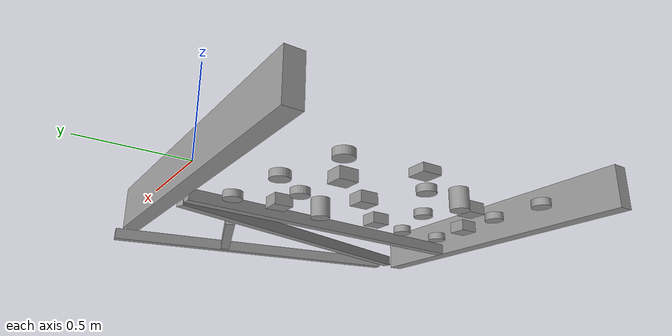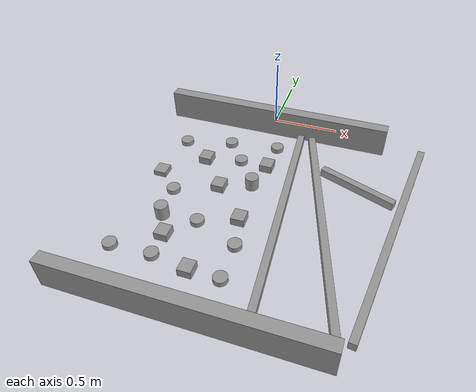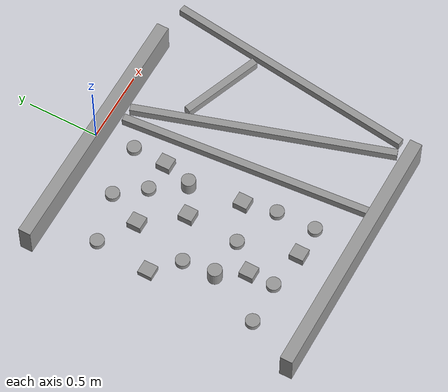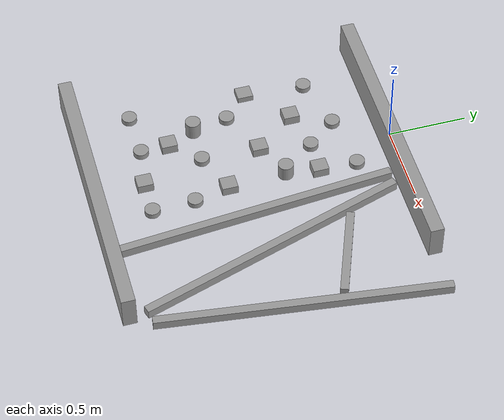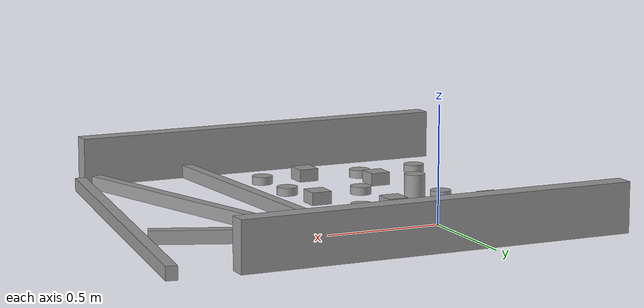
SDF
<?xml version='1.0'?>
<sdf version='1.7'>
  <model name='complex_terrain'>
    <link name='link'>
      <inertial>
        <mass>1</mass>
        <inertia>
          <ixx>0.166667</ixx>
          <ixy>0</ixy>
          <ixz>0</ixz>
          <iyy>0.166667</iyy>
          <iyz>0</iyz>
          <izz>0.166667</izz>
        </inertia>
        <pose>0 0 0 0 -0 0</pose>
      </inertial>
      <self_collide>0</self_collide>
      <enable_wind>0</enable_wind>
      <kinematic>0</kinematic>
      <pose>0 0 0 0 -0 0</pose>
      <gravity>1</gravity>
      <visual name='visual'>
        <geometry>
          <box>
            <size>1.79287 0.085937 0.224799</size>
          </box>
        </geometry>
        <material>
          <script>
            <name>Gazebo/Grey</name>
            <uri>file://media/materials/scripts/gazebo.material</uri>
          </script>
          <shader type='pixel'>
            <normal_map>__default__</normal_map>
          </shader>
          <ambient>1 1 1 1</ambient>
          <diffuse>0.7 0.7 0.7 1</diffuse>
          <specular>0.01 0.01 0.01 1</specular>
          <emissive>0 0 0 1</emissive>
        </material>
        <pose>0 0 0 0 -0 0</pose>
        <transparency>0</transparency>
        <cast_shadows>1</cast_shadows>
      </visual>
      <collision name='collision'>
        <laser_retro>0</laser_retro>
        <max_contacts>10</max_contacts>
        <pose>0 0 0 0 -0 0</pose>
        <geometry>
          <box>
            <size>1.79287 0.085937 0.224799</size>
          </box>
        </geometry>
        <surface>
          <friction>
            <ode>
              <mu>1</mu>
              <mu2>1</mu2>
              <fdir1>0 0 0</fdir1>
              <slip1>0</slip1>
              <slip2>0</slip2>
            </ode>
            <torsional>
              <coefficient>1</coefficient>
              <patch_radius>0</patch_radius>
              <surface_radius>0</surface_radius>
              <use_patch_radius>1</use_patch_radius>
              <ode>
                <slip>0</slip>
              </ode>
            </torsional>
          </friction>
          <bounce>
            <restitution_coefficient>0</restitution_coefficient>
            <threshold>1e+06</threshold>
          </bounce>
          <contact>
            <collide_without_contact>0</collide_without_contact>
            <collide_without_contact_bitmask>1</collide_without_contact_bitmask>
            <collide_bitmask>1</collide_bitmask>
            <ode>
              <soft_cfm>0</soft_cfm>
              <soft_erp>0.2</soft_erp>
              <kp>1e+13</kp>
              <kd>1</kd>
              <max_vel>0.01</max_vel>
              <min_depth>0</min_depth>
            </ode>
            <bullet>
              <split_impulse>1</split_impulse>
              <split_impulse_penetration_threshold>-0.01</split_impulse_penetration_threshold>
              <soft_cfm>0</soft_cfm>
              <soft_erp>0.2</soft_erp>
              <kp>1e+13</kp>
              <kd>1</kd>
            </bullet>
          </contact>
        </surface>
      </collision>
    </link>
    <link name='link_1'>
      <inertial>
        <mass>0.00035226</mass>
        <inertia>
          <ixx>2.5e-07</ixx>
          <ixy>0</ixy>
          <ixz>0</ixz>
          <iyy>2.5e-07</iyy>
          <iyz>0</iyz>
          <izz>4.2e-07</izz>
        </inertia>
        <pose>0 0 0 0 -0 0</pose>
      </inertial>
      <pose>-0.496384 -0.928451 -0.09349 -1e-06 4.2e-05 3e-05</pose>
      <gravity>1</gravity>
      <self_collide>0</self_collide>
      <kinematic>0</kinematic>
      <enable_wind>0</enable_wind>
      <visual name='visual'>
        <pose>0 0 0 0 -0 0</pose>
        <geometry>
          <cylinder>
            <radius>0.048621</radius>
            <length>0.0373063</length>
          </cylinder>
        </geometry>
        <material>
          <lighting>1</lighting>
          <script>
            <uri>file://media/materials/scripts/gazebo.material</uri>
            <name>Gazebo/Grey</name>
          </script>
          <shader type='pixel'>
            <normal_map>__default__</normal_map>
          </shader>
          <ambient>1 1 1 1</ambient>
          <diffuse>0.7 0.7 0.7 1</diffuse>
          <specular>0.01 0.01 0.01 1</specular>
          <emissive>0 0 0 1</emissive>
        </material>
        <transparency>0</transparency>
        <cast_shadows>1</cast_shadows>
      </visual>
      <collision name='collision'>
        <laser_retro>0</laser_retro>
        <max_contacts>10</max_contacts>
        <pose>0 0 0 0 -0 0</pose>
        <geometry>
          <cylinder>
            <radius>0.048621</radius>
            <length>0.037306</length>
          </cylinder>
        </geometry>
        <surface>
          <friction>
            <ode>
              <mu>1</mu>
              <mu2>1</mu2>
              <fdir1>0 0 0</fdir1>
              <slip1>0</slip1>
              <slip2>0</slip2>
            </ode>
            <torsional>
              <coefficient>1</coefficient>
              <patch_radius>0</patch_radius>
              <surface_radius>0</surface_radius>
              <use_patch_radius>1</use_patch_radius>
              <ode>
                <slip>0</slip>
              </ode>
            </torsional>
          </friction>
          <bounce>
            <restitution_coefficient>0</restitution_coefficient>
            <threshold>1e+06</threshold>
          </bounce>
          <contact>
            <collide_without_contact>0</collide_without_contact>
            <collide_without_contact_bitmask>1</collide_without_contact_bitmask>
            <collide_bitmask>1</collide_bitmask>
            <ode>
              <soft_cfm>0</soft_cfm>
              <soft_erp>0.2</soft_erp>
              <kp>1e+13</kp>
              <kd>1</kd>
              <max_vel>0.01</max_vel>
              <min_depth>0</min_depth>
            </ode>
            <bullet>
              <split_impulse>1</split_impulse>
              <split_impulse_penetration_threshold>-0.01</split_impulse_penetration_threshold>
              <soft_cfm>0</soft_cfm>
              <soft_erp>0.2</soft_erp>
              <kp>1e+13</kp>
              <kd>1</kd>
            </bullet>
          </contact>
        </surface>
      </collision>
    </link>
    <link name='link_1_clone'>
      <inertial>
        <mass>0.00035226</mass>
        <inertia>
          <ixx>2.5e-07</ixx>
          <ixy>0</ixy>
          <ixz>0</ixz>
          <iyy>2.5e-07</iyy>
          <iyz>0</iyz>
          <izz>4.2e-07</izz>
        </inertia>
        <pose>0 0 0 0 -0 0</pose>
      </inertial>
      <pose>-0.136256 -0.473534 -0.093484 -2e-06 8.4e-05 6e-05</pose>
      <gravity>1</gravity>
      <self_collide>0</self_collide>
      <kinematic>0</kinematic>
      <enable_wind>0</enable_wind>
      <visual name='visual'>
        <pose>0 0 0 0 -0 0</pose>
        <geometry>
          <cylinder>
            <radius>0.048621</radius>
            <length>0.0373063</length>
          </cylinder>
        </geometry>
        <material>
          <lighting>1</lighting>
          <script>
            <uri>file://media/materials/scripts/gazebo.material</uri>
            <name>Gazebo/Grey</name>
          </script>
          <shader type='pixel'>
            <normal_map>__default__</normal_map>
          </shader>
          <ambient>1 1 1 1</ambient>
          <diffuse>0.7 0.7 0.7 1</diffuse>
          <specular>0.01 0.01 0.01 1</specular>
          <emissive>0 0 0 1</emissive>
        </material>
        <transparency>0</transparency>
        <cast_shadows>1</cast_shadows>
      </visual>
      <collision name='collision'>
        <laser_retro>0</laser_retro>
        <max_contacts>10</max_contacts>
        <pose>0 0 0 0 -0 0</pose>
        <geometry>
          <cylinder>
            <radius>0.048621</radius>
            <length>0.037306</length>
          </cylinder>
        </geometry>
        <surface>
          <friction>
            <ode>
              <mu>1</mu>
              <mu2>1</mu2>
              <fdir1>0 0 0</fdir1>
              <slip1>0</slip1>
              <slip2>0</slip2>
            </ode>
            <torsional>
              <coefficient>1</coefficient>
              <patch_radius>0</patch_radius>
              <surface_radius>0</surface_radius>
              <use_patch_radius>1</use_patch_radius>
              <ode>
                <slip>0</slip>
              </ode>
            </torsional>
          </friction>
          <bounce>
            <restitution_coefficient>0</restitution_coefficient>
            <threshold>1e+06</threshold>
          </bounce>
          <contact>
            <collide_without_contact>0</collide_without_contact>
            <collide_without_contact_bitmask>1</collide_without_contact_bitmask>
            <collide_bitmask>1</collide_bitmask>
            <ode>
              <soft_cfm>0</soft_cfm>
              <soft_erp>0.2</soft_erp>
              <kp>1e+13</kp>
              <kd>1</kd>
              <max_vel>0.01</max_vel>
              <min_depth>0</min_depth>
            </ode>
            <bullet>
              <split_impulse>1</split_impulse>
              <split_impulse_penetration_threshold>-0.01</split_impulse_penetration_threshold>
              <soft_cfm>0</soft_cfm>
              <soft_erp>0.2</soft_erp>
              <kp>1e+13</kp>
              <kd>1</kd>
            </bullet>
          </contact>
        </surface>
      </collision>
    </link>
    <link name='link_1_clone_0'>
      <inertial>
        <mass>0.00035226</mass>
        <inertia>
          <ixx>2.5e-07</ixx>
          <ixy>0</ixy>
          <ixz>0</ixz>
          <iyy>2.5e-07</iyy>
          <iyz>0</iyz>
          <izz>4.2e-07</izz>
        </inertia>
        <pose>0 0 0 0 -0 0</pose>
      </inertial>
      <pose>-0.205542 -1.16693 -0.09348 -2e-06 8.4e-05 6e-05</pose>
      <gravity>1</gravity>
      <self_collide>0</self_collide>
      <kinematic>0</kinematic>
      <enable_wind>0</enable_wind>
      <visual name='visual'>
        <pose>0 0 0 0 -0 0</pose>
        <geometry>
          <cylinder>
            <radius>0.048621</radius>
            <length>0.0373063</length>
          </cylinder>
        </geometry>
        <material>
          <lighting>1</lighting>
          <script>
            <uri>file://media/materials/scripts/gazebo.material</uri>
            <name>Gazebo/Grey</name>
          </script>
          <shader type='pixel'>
            <normal_map>__default__</normal_map>
          </shader>
          <ambient>1 1 1 1</ambient>
          <diffuse>0.7 0.7 0.7 1</diffuse>
          <specular>0.01 0.01 0.01 1</specular>
          <emissive>0 0 0 1</emissive>
        </material>
        <transparency>0</transparency>
        <cast_shadows>1</cast_shadows>
      </visual>
      <collision name='collision'>
        <laser_retro>0</laser_retro>
        <max_contacts>10</max_contacts>
        <pose>0 0 0 0 -0 0</pose>
        <geometry>
          <cylinder>
            <radius>0.048621</radius>
            <length>0.037306</length>
          </cylinder>
        </geometry>
        <surface>
          <friction>
            <ode>
              <mu>1</mu>
              <mu2>1</mu2>
              <fdir1>0 0 0</fdir1>
              <slip1>0</slip1>
              <slip2>0</slip2>
            </ode>
            <torsional>
              <coefficient>1</coefficient>
              <patch_radius>0</patch_radius>
              <surface_radius>0</surface_radius>
              <use_patch_radius>1</use_patch_radius>
              <ode>
                <slip>0</slip>
              </ode>
            </torsional>
          </friction>
          <bounce>
            <restitution_coefficient>0</restitution_coefficient>
            <threshold>1e+06</threshold>
          </bounce>
          <contact>
            <collide_without_contact>0</collide_without_contact>
            <collide_without_contact_bitmask>1</collide_without_contact_bitmask>
            <collide_bitmask>1</collide_bitmask>
            <ode>
              <soft_cfm>0</soft_cfm>
              <soft_erp>0.2</soft_erp>
              <kp>1e+13</kp>
              <kd>1</kd>
              <max_vel>0.01</max_vel>
              <min_depth>0</min_depth>
            </ode>
            <bullet>
              <split_impulse>1</split_impulse>
              <split_impulse_penetration_threshold>-0.01</split_impulse_penetration_threshold>
              <soft_cfm>0</soft_cfm>
              <soft_erp>0.2</soft_erp>
              <kp>1e+13</kp>
              <kd>1</kd>
            </bullet>
          </contact>
        </surface>
      </collision>
    </link>
    <link name='link_1_clone_1'>
      <inertial>
        <mass>0.00095797</mass>
        <inertia>
          <ixx>1.39e-06</ixx>
          <ixy>0</ixy>
          <ixz>0</ixz>
          <iyy>1.39e-06</iyy>
          <iyz>0</iyz>
          <izz>1.13e-06</izz>
        </inertia>
        <pose>0 0 0 0 -0 0</pose>
      </inertial>
      <pose>0.021202 -0.683142 -0.09349 -2e-06 8.4e-05 6e-05</pose>
      <gravity>1</gravity>
      <self_collide>0</self_collide>
      <kinematic>0</kinematic>
      <enable_wind>0</enable_wind>
      <visual name='visual'>
        <pose>0 0 0 0 -0 0</pose>
        <geometry>
          <cylinder>
            <radius>0.048621</radius>
            <length>0.101455</length>
          </cylinder>
        </geometry>
        <material>
          <lighting>1</lighting>
          <script>
            <uri>file://media/materials/scripts/gazebo.material</uri>
            <name>Gazebo/Grey</name>
          </script>
          <shader type='pixel'>
            <normal_map>__default__</normal_map>
          </shader>
          <ambient>1 1 1 1</ambient>
          <diffuse>0.7 0.7 0.7 1</diffuse>
          <specular>0.01 0.01 0.01 1</specular>
          <emissive>0 0 0 1</emissive>
        </material>
        <transparency>0</transparency>
        <cast_shadows>1</cast_shadows>
      </visual>
      <collision name='collision'>
        <laser_retro>0</laser_retro>
        <max_contacts>10</max_contacts>
        <pose>0 0 0 0 -0 0</pose>
        <geometry>
          <cylinder>
            <radius>0.048621</radius>
            <length>0.101455</length>
          </cylinder>
        </geometry>
        <surface>
          <friction>
            <ode>
              <mu>1</mu>
              <mu2>1</mu2>
              <fdir1>0 0 0</fdir1>
              <slip1>0</slip1>
              <slip2>0</slip2>
            </ode>
            <torsional>
              <coefficient>1</coefficient>
              <patch_radius>0</patch_radius>
              <surface_radius>0</surface_radius>
              <use_patch_radius>1</use_patch_radius>
              <ode>
                <slip>0</slip>
              </ode>
            </torsional>
          </friction>
          <bounce>
            <restitution_coefficient>0</restitution_coefficient>
            <threshold>1e+06</threshold>
          </bounce>
          <contact>
            <collide_without_contact>0</collide_without_contact>
            <collide_without_contact_bitmask>1</collide_without_contact_bitmask>
            <collide_bitmask>1</collide_bitmask>
            <ode>
              <soft_cfm>0</soft_cfm>
              <soft_erp>0.2</soft_erp>
              <kp>1e+13</kp>
              <kd>1</kd>
              <max_vel>0.01</max_vel>
              <min_depth>0</min_depth>
            </ode>
            <bullet>
              <split_impulse>1</split_impulse>
              <split_impulse_penetration_threshold>-0.01</split_impulse_penetration_threshold>
              <soft_cfm>0</soft_cfm>
              <soft_erp>0.2</soft_erp>
              <kp>1e+13</kp>
              <kd>1</kd>
            </bullet>
          </contact>
        </surface>
      </collision>
    </link>
    <link name='link_1_clone_2'>
      <inertial>
        <mass>0.00103254</mass>
        <inertia>
          <ixx>1.64e-06</ixx>
          <ixy>0</ixy>
          <ixz>0</ixz>
          <iyy>1.64e-06</iyy>
          <iyz>0</iyz>
          <izz>1.22e-06</izz>
        </inertia>
        <pose>0 0 0 0 -0 0</pose>
      </inertial>
      <pose>-0.478003 -1.15427 -0.093468 -2e-06 8.4e-05 6e-05</pose>
      <self_collide>0</self_collide>
      <enable_wind>0</enable_wind>
      <kinematic>0</kinematic>
      <gravity>1</gravity>
      <visual name='visual'>
        <pose>0 0 0 0 -0 0</pose>
        <geometry>
          <cylinder>
            <radius>0.048621</radius>
            <length>0.109347</length>
          </cylinder>
        </geometry>
        <material>
          <lighting>1</lighting>
          <script>
            <uri>file://media/materials/scripts/gazebo.material</uri>
            <name>Gazebo/Grey</name>
          </script>
          <shader type='pixel'>
            <normal_map>__default__</normal_map>
          </shader>
          <ambient>1 1 1 1</ambient>
          <diffuse>0.7 0.7 0.7 1</diffuse>
          <specular>0.01 0.01 0.01 1</specular>
          <emissive>0 0 0 1</emissive>
        </material>
        <transparency>0</transparency>
        <cast_shadows>1</cast_shadows>
      </visual>
      <collision name='collision'>
        <laser_retro>0</laser_retro>
        <max_contacts>10</max_contacts>
        <pose>0 0 0 0 -0 0</pose>
        <geometry>
          <cylinder>
            <radius>0.048621</radius>
            <length>0.109347</length>
          </cylinder>
        </geometry>
        <surface>
          <friction>
            <ode>
              <mu>1</mu>
              <mu2>1</mu2>
              <fdir1>0 0 0</fdir1>
              <slip1>0</slip1>
              <slip2>0</slip2>
            </ode>
            <torsional>
              <coefficient>1</coefficient>
              <patch_radius>0</patch_radius>
              <surface_radius>0</surface_radius>
              <use_patch_radius>1</use_patch_radius>
              <ode>
                <slip>0</slip>
              </ode>
            </torsional>
          </friction>
          <bounce>
            <restitution_coefficient>0</restitution_coefficient>
            <threshold>1e+06</threshold>
          </bounce>
          <contact>
            <collide_without_contact>0</collide_without_contact>
            <collide_without_contact_bitmask>1</collide_without_contact_bitmask>
            <collide_bitmask>1</collide_bitmask>
            <ode>
              <soft_cfm>0</soft_cfm>
              <soft_erp>0.2</soft_erp>
              <kp>1e+13</kp>
              <kd>1</kd>
              <max_vel>0.01</max_vel>
              <min_depth>0</min_depth>
            </ode>
            <bullet>
              <split_impulse>1</split_impulse>
              <split_impulse_penetration_threshold>-0.01</split_impulse_penetration_threshold>
              <soft_cfm>0</soft_cfm>
              <soft_erp>0.2</soft_erp>
              <kp>1e+13</kp>
              <kd>1</kd>
            </bullet>
          </contact>
        </surface>
      </collision>
    </link>
    <link name='link_1_clone_3'>
      <inertial>
        <mass>0.00035226</mass>
        <inertia>
          <ixx>2.5e-07</ixx>
          <ixy>0</ixy>
          <ixz>0</ixz>
          <iyy>2.5e-07</iyy>
          <iyz>0</iyz>
          <izz>4.2e-07</izz>
        </inertia>
        <pose>0 0 0 0 -0 0</pose>
      </inertial>
      <pose>-0.635782 -0.37601 -0.093463 -2e-06 8.4e-05 6e-05</pose>
      <gravity>1</gravity>
      <self_collide>0</self_collide>
      <kinematic>0</kinematic>
      <enable_wind>0</enable_wind>
      <visual name='visual'>
        <pose>0 0 0 0 -0 0</pose>
        <geometry>
          <cylinder>
            <radius>0.048621</radius>
            <length>0.0373063</length>
          </cylinder>
        </geometry>
        <material>
          <lighting>1</lighting>
          <script>
            <uri>file://media/materials/scripts/gazebo.material</uri>
            <name>Gazebo/Grey</name>
          </script>
          <shader type='pixel'>
            <normal_map>__default__</normal_map>
          </shader>
          <ambient>1 1 1 1</ambient>
          <diffuse>0.7 0.7 0.7 1</diffuse>
          <specular>0.01 0.01 0.01 1</specular>
          <emissive>0 0 0 1</emissive>
        </material>
        <transparency>0</transparency>
        <cast_shadows>1</cast_shadows>
      </visual>
      <collision name='collision'>
        <laser_retro>0</laser_retro>
        <max_contacts>10</max_contacts>
        <pose>0 0 0 0 -0 0</pose>
        <geometry>
          <cylinder>
            <radius>0.048621</radius>
            <length>0.037306</length>
          </cylinder>
        </geometry>
        <surface>
          <friction>
            <ode>
              <mu>1</mu>
              <mu2>1</mu2>
              <fdir1>0 0 0</fdir1>
              <slip1>0</slip1>
              <slip2>0</slip2>
            </ode>
            <torsional>
              <coefficient>1</coefficient>
              <patch_radius>0</patch_radius>
              <surface_radius>0</surface_radius>
              <use_patch_radius>1</use_patch_radius>
              <ode>
                <slip>0</slip>
              </ode>
            </torsional>
          </friction>
          <bounce>
            <restitution_coefficient>0</restitution_coefficient>
            <threshold>1e+06</threshold>
          </bounce>
          <contact>
            <collide_without_contact>0</collide_without_contact>
            <collide_without_contact_bitmask>1</collide_without_contact_bitmask>
            <collide_bitmask>1</collide_bitmask>
            <ode>
              <soft_cfm>0</soft_cfm>
              <soft_erp>0.2</soft_erp>
              <kp>1e+13</kp>
              <kd>1</kd>
              <max_vel>0.01</max_vel>
              <min_depth>0</min_depth>
            </ode>
            <bullet>
              <split_impulse>1</split_impulse>
              <split_impulse_penetration_threshold>-0.01</split_impulse_penetration_threshold>
              <soft_cfm>0</soft_cfm>
              <soft_erp>0.2</soft_erp>
              <kp>1e+13</kp>
              <kd>1</kd>
            </bullet>
          </contact>
        </surface>
      </collision>
    </link>
    <link name='link_1_clone_4'>
      <inertial>
        <mass>0.00035226</mass>
        <inertia>
          <ixx>2.5e-07</ixx>
          <ixy>0</ixy>
          <ixz>0</ixz>
          <iyy>2.5e-07</iyy>
          <iyz>0</iyz>
          <izz>4.2e-07</izz>
        </inertia>
        <pose>0 0 0 0 -0 0</pose>
      </inertial>
      <pose>-0.284409 -0.2871 -0.093478 -2e-06 8.4e-05 6e-05</pose>
      <gravity>1</gravity>
      <self_collide>0</self_collide>
      <kinematic>0</kinematic>
      <enable_wind>0</enable_wind>
      <visual name='visual'>
        <pose>0 0 0 0 -0 0</pose>
        <geometry>
          <cylinder>
            <radius>0.048621</radius>
            <length>0.0373063</length>
          </cylinder>
        </geometry>
        <material>
          <lighting>1</lighting>
          <script>
            <uri>file://media/materials/scripts/gazebo.material</uri>
            <name>Gazebo/Grey</name>
          </script>
          <shader type='pixel'>
            <normal_map>__default__</normal_map>
          </shader>
          <ambient>1 1 1 1</ambient>
          <diffuse>0.7 0.7 0.7 1</diffuse>
          <specular>0.01 0.01 0.01 1</specular>
          <emissive>0 0 0 1</emissive>
        </material>
        <transparency>0</transparency>
        <cast_shadows>1</cast_shadows>
      </visual>
      <collision name='collision'>
        <laser_retro>0</laser_retro>
        <max_contacts>10</max_contacts>
        <pose>0 0 0 0 -0 0</pose>
        <geometry>
          <cylinder>
            <radius>0.048621</radius>
            <length>0.037306</length>
          </cylinder>
        </geometry>
        <surface>
          <friction>
            <ode>
              <mu>1</mu>
              <mu2>1</mu2>
              <fdir1>0 0 0</fdir1>
              <slip1>0</slip1>
              <slip2>0</slip2>
            </ode>
            <torsional>
              <coefficient>1</coefficient>
              <patch_radius>0</patch_radius>
              <surface_radius>0</surface_radius>
              <use_patch_radius>1</use_patch_radius>
              <ode>
                <slip>0</slip>
              </ode>
            </torsional>
          </friction>
          <bounce>
            <restitution_coefficient>0</restitution_coefficient>
            <threshold>1e+06</threshold>
          </bounce>
          <contact>
            <collide_without_contact>0</collide_without_contact>
            <collide_without_contact_bitmask>1</collide_without_contact_bitmask>
            <collide_bitmask>1</collide_bitmask>
            <ode>
              <soft_cfm>0</soft_cfm>
              <soft_erp>0.2</soft_erp>
              <kp>1e+13</kp>
              <kd>1</kd>
              <max_vel>0.01</max_vel>
              <min_depth>0</min_depth>
            </ode>
            <bullet>
              <split_impulse>1</split_impulse>
              <split_impulse_penetration_threshold>-0.01</split_impulse_penetration_threshold>
              <soft_cfm>0</soft_cfm>
              <soft_erp>0.2</soft_erp>
              <kp>1e+13</kp>
              <kd>1</kd>
            </bullet>
          </contact>
        </surface>
      </collision>
    </link>
    <link name='link_1_clone_5'>
      <inertial>
        <mass>0.00035226</mass>
        <inertia>
          <ixx>2.5e-07</ixx>
          <ixy>0</ixy>
          <ixz>0</ixz>
          <iyy>2.5e-07</iyy>
          <iyz>0</iyz>
          <izz>4.2e-07</izz>
        </inertia>
        <pose>0 0 0 0 -0 0</pose>
      </inertial>
      <pose>-0.366811 -1.52069 -0.093473 -2e-06 8.4e-05 6e-05</pose>
      <gravity>1</gravity>
      <self_collide>0</self_collide>
      <kinematic>0</kinematic>
      <enable_wind>0</enable_wind>
      <visual name='visual'>
        <pose>0 0 0 0 -0 0</pose>
        <geometry>
          <cylinder>
            <radius>0.048621</radius>
            <length>0.0373063</length>
          </cylinder>
        </geometry>
        <material>
          <lighting>1</lighting>
          <script>
            <uri>file://media/materials/scripts/gazebo.material</uri>
            <name>Gazebo/Grey</name>
          </script>
          <shader type='pixel'>
            <normal_map>__default__</normal_map>
          </shader>
          <ambient>1 1 1 1</ambient>
          <diffuse>0.7 0.7 0.7 1</diffuse>
          <specular>0.01 0.01 0.01 1</specular>
          <emissive>0 0 0 1</emissive>
        </material>
        <transparency>0</transparency>
        <cast_shadows>1</cast_shadows>
      </visual>
      <collision name='collision'>
        <laser_retro>0</laser_retro>
        <max_contacts>10</max_contacts>
        <pose>0 0 0 0 -0 0</pose>
        <geometry>
          <cylinder>
            <radius>0.048621</radius>
            <length>0.037306</length>
          </cylinder>
        </geometry>
        <surface>
          <friction>
            <ode>
              <mu>1</mu>
              <mu2>1</mu2>
              <fdir1>0 0 0</fdir1>
              <slip1>0</slip1>
              <slip2>0</slip2>
            </ode>
            <torsional>
              <coefficient>1</coefficient>
              <patch_radius>0</patch_radius>
              <surface_radius>0</surface_radius>
              <use_patch_radius>1</use_patch_radius>
              <ode>
                <slip>0</slip>
              </ode>
            </torsional>
          </friction>
          <bounce>
            <restitution_coefficient>0</restitution_coefficient>
            <threshold>1e+06</threshold>
          </bounce>
          <contact>
            <collide_without_contact>0</collide_without_contact>
            <collide_without_contact_bitmask>1</collide_without_contact_bitmask>
            <collide_bitmask>1</collide_bitmask>
            <ode>
              <soft_cfm>0</soft_cfm>
              <soft_erp>0.2</soft_erp>
              <kp>1e+13</kp>
              <kd>1</kd>
              <max_vel>0.01</max_vel>
              <min_depth>0</min_depth>
            </ode>
            <bullet>
              <split_impulse>1</split_impulse>
              <split_impulse_penetration_threshold>-0.01</split_impulse_penetration_threshold>
              <soft_cfm>0</soft_cfm>
              <soft_erp>0.2</soft_erp>
              <kp>1e+13</kp>
              <kd>1</kd>
            </bullet>
          </contact>
        </surface>
      </collision>
    </link>
    <link name='link_1_clone_6'>
      <inertial>
        <mass>0.00035226</mass>
        <inertia>
          <ixx>2.5e-07</ixx>
          <ixy>0</ixy>
          <ixz>0</ixz>
          <iyy>2.5e-07</iyy>
          <iyz>0</iyz>
          <izz>4.2e-07</izz>
        </inertia>
        <pose>0 0 0 0 -0 0</pose>
      </inertial>
      <pose>-0.661559 -1.52878 -0.09346 -2e-06 8.4e-05 6e-05</pose>
      <gravity>1</gravity>
      <self_collide>0</self_collide>
      <kinematic>0</kinematic>
      <enable_wind>0</enable_wind>
      <visual name='visual'>
        <pose>0 0 0 0 -0 0</pose>
        <geometry>
          <cylinder>
            <radius>0.048621</radius>
            <length>0.0373063</length>
          </cylinder>
        </geometry>
        <material>
          <lighting>1</lighting>
          <script>
            <uri>file://media/materials/scripts/gazebo.material</uri>
            <name>Gazebo/Grey</name>
          </script>
          <shader type='pixel'>
            <normal_map>__default__</normal_map>
          </shader>
          <ambient>1 1 1 1</ambient>
          <diffuse>0.7 0.7 0.7 1</diffuse>
          <specular>0.01 0.01 0.01 1</specular>
          <emissive>0 0 0 1</emissive>
        </material>
        <transparency>0</transparency>
        <cast_shadows>1</cast_shadows>
      </visual>
      <collision name='collision'>
        <laser_retro>0</laser_retro>
        <max_contacts>10</max_contacts>
        <pose>0 0 0 0 -0 0</pose>
        <geometry>
          <cylinder>
            <radius>0.048621</radius>
            <length>0.037306</length>
          </cylinder>
        </geometry>
        <surface>
          <friction>
            <ode>
              <mu>1</mu>
              <mu2>1</mu2>
              <fdir1>0 0 0</fdir1>
              <slip1>0</slip1>
              <slip2>0</slip2>
            </ode>
            <torsional>
              <coefficient>1</coefficient>
              <patch_radius>0</patch_radius>
              <surface_radius>0</surface_radius>
              <use_patch_radius>1</use_patch_radius>
              <ode>
                <slip>0</slip>
              </ode>
            </torsional>
          </friction>
          <bounce>
            <restitution_coefficient>0</restitution_coefficient>
            <threshold>1e+06</threshold>
          </bounce>
          <contact>
            <collide_without_contact>0</collide_without_contact>
            <collide_without_contact_bitmask>1</collide_without_contact_bitmask>
            <collide_bitmask>1</collide_bitmask>
            <ode>
              <soft_cfm>0</soft_cfm>
              <soft_erp>0.2</soft_erp>
              <kp>1e+13</kp>
              <kd>1</kd>
              <max_vel>0.01</max_vel>
              <min_depth>0</min_depth>
            </ode>
            <bullet>
              <split_impulse>1</split_impulse>
              <split_impulse_penetration_threshold>-0.01</split_impulse_penetration_threshold>
              <soft_cfm>0</soft_cfm>
              <soft_erp>0.2</soft_erp>
              <kp>1e+13</kp>
              <kd>1</kd>
            </bullet>
          </contact>
        </surface>
      </collision>
    </link>
    <link name='link_1_clone_7'>
      <inertial>
        <mass>0.00035226</mass>
        <inertia>
          <ixx>2.5e-07</ixx>
          <ixy>0</ixy>
          <ixz>0</ixz>
          <iyy>2.5e-07</iyy>
          <iyz>0</iyz>
          <izz>4.2e-07</izz>
        </inertia>
        <pose>0 0 0 0 -0 0</pose>
      </inertial>
      <pose>0.119527 -1.56335 -0.093493 -2e-06 8.4e-05 6e-05</pose>
      <gravity>1</gravity>
      <self_collide>0</self_collide>
      <kinematic>0</kinematic>
      <enable_wind>0</enable_wind>
      <visual name='visual'>
        <pose>0 0 0 0 -0 0</pose>
        <geometry>
          <cylinder>
            <radius>0.048621</radius>
            <length>0.0373063</length>
          </cylinder>
        </geometry>
        <material>
          <lighting>1</lighting>
          <script>
            <uri>file://media/materials/scripts/gazebo.material</uri>
            <name>Gazebo/Grey</name>
          </script>
          <shader type='pixel'>
            <normal_map>__default__</normal_map>
          </shader>
          <ambient>1 1 1 1</ambient>
          <diffuse>0.7 0.7 0.7 1</diffuse>
          <specular>0.01 0.01 0.01 1</specular>
          <emissive>0 0 0 1</emissive>
        </material>
        <transparency>0</transparency>
        <cast_shadows>1</cast_shadows>
      </visual>
      <collision name='collision'>
        <laser_retro>0</laser_retro>
        <max_contacts>10</max_contacts>
        <pose>0 0 0 0 -0 0</pose>
        <geometry>
          <cylinder>
            <radius>0.048621</radius>
            <length>0.037306</length>
          </cylinder>
        </geometry>
        <surface>
          <friction>
            <ode>
              <mu>1</mu>
              <mu2>1</mu2>
              <fdir1>0 0 0</fdir1>
              <slip1>0</slip1>
              <slip2>0</slip2>
            </ode>
            <torsional>
              <coefficient>1</coefficient>
              <patch_radius>0</patch_radius>
              <surface_radius>0</surface_radius>
              <use_patch_radius>1</use_patch_radius>
              <ode>
                <slip>0</slip>
              </ode>
            </torsional>
          </friction>
          <bounce>
            <restitution_coefficient>0</restitution_coefficient>
            <threshold>1e+06</threshold>
          </bounce>
          <contact>
            <collide_without_contact>0</collide_without_contact>
            <collide_without_contact_bitmask>1</collide_without_contact_bitmask>
            <collide_bitmask>1</collide_bitmask>
            <ode>
              <soft_cfm>0</soft_cfm>
              <soft_erp>0.2</soft_erp>
              <kp>1e+13</kp>
              <kd>1</kd>
              <max_vel>0.01</max_vel>
              <min_depth>0</min_depth>
            </ode>
            <bullet>
              <split_impulse>1</split_impulse>
              <split_impulse_penetration_threshold>-0.01</split_impulse_penetration_threshold>
              <soft_cfm>0</soft_cfm>
              <soft_erp>0.2</soft_erp>
              <kp>1e+13</kp>
              <kd>1</kd>
            </bullet>
          </contact>
        </surface>
      </collision>
    </link>
    <link name='link_1_clone_8'>
      <inertial>
        <mass>0.00035226</mass>
        <inertia>
          <ixx>2.5e-07</ixx>
          <ixy>0</ixy>
          <ixz>0</ixz>
          <iyy>2.5e-07</iyy>
          <iyz>0</iyz>
          <izz>4.2e-07</izz>
        </inertia>
        <pose>0 0 0 0 -0 0</pose>
      </inertial>
      <pose>0.111307 -1.28956 -0.093493 -2e-06 8.4e-05 6e-05</pose>
      <gravity>1</gravity>
      <self_collide>0</self_collide>
      <kinematic>0</kinematic>
      <enable_wind>0</enable_wind>
      <visual name='visual'>
        <pose>0 0 0 0 -0 0</pose>
        <geometry>
          <cylinder>
            <radius>0.048621</radius>
            <length>0.0373063</length>
          </cylinder>
        </geometry>
        <material>
          <lighting>1</lighting>
          <script>
            <uri>file://media/materials/scripts/gazebo.material</uri>
            <name>Gazebo/Grey</name>
          </script>
          <shader type='pixel'>
            <normal_map>__default__</normal_map>
          </shader>
          <ambient>1 1 1 1</ambient>
          <diffuse>0.7 0.7 0.7 1</diffuse>
          <specular>0.01 0.01 0.01 1</specular>
          <emissive>0 0 0 1</emissive>
        </material>
        <transparency>0</transparency>
        <cast_shadows>1</cast_shadows>
      </visual>
      <collision name='collision'>
        <laser_retro>0</laser_retro>
        <max_contacts>10</max_contacts>
        <pose>0 0 0 0 -0 0</pose>
        <geometry>
          <cylinder>
            <radius>0.048621</radius>
            <length>0.037306</length>
          </cylinder>
        </geometry>
        <surface>
          <friction>
            <ode>
              <mu>1</mu>
              <mu2>1</mu2>
              <fdir1>0 0 0</fdir1>
              <slip1>0</slip1>
              <slip2>0</slip2>
            </ode>
            <torsional>
              <coefficient>1</coefficient>
              <patch_radius>0</patch_radius>
              <surface_radius>0</surface_radius>
              <use_patch_radius>1</use_patch_radius>
              <ode>
                <slip>0</slip>
              </ode>
            </torsional>
          </friction>
          <bounce>
            <restitution_coefficient>0</restitution_coefficient>
            <threshold>1e+06</threshold>
          </bounce>
          <contact>
            <collide_without_contact>0</collide_without_contact>
            <collide_without_contact_bitmask>1</collide_without_contact_bitmask>
            <collide_bitmask>1</collide_bitmask>
            <ode>
              <soft_cfm>0</soft_cfm>
              <soft_erp>0.2</soft_erp>
              <kp>1e+13</kp>
              <kd>1</kd>
              <max_vel>0.01</max_vel>
              <min_depth>0</min_depth>
            </ode>
            <bullet>
              <split_impulse>1</split_impulse>
              <split_impulse_penetration_threshold>-0.01</split_impulse_penetration_threshold>
              <soft_cfm>0</soft_cfm>
              <soft_erp>0.2</soft_erp>
              <kp>1e+13</kp>
              <kd>1</kd>
            </bullet>
          </contact>
        </surface>
      </collision>
    </link>
    <link name='link_1_clone_9'>
      <inertial>
        <mass>0.00035226</mass>
        <inertia>
          <ixx>2.5e-07</ixx>
          <ixy>0</ixy>
          <ixz>0</ixz>
          <iyy>2.5e-07</iyy>
          <iyz>0</iyz>
          <izz>4.2e-07</izz>
        </inertia>
        <pose>0 0 0 0 -0 0</pose>
      </inertial>
      <pose>0.085398 -0.237561 -0.093493 -2e-06 8.4e-05 6e-05</pose>
      <gravity>1</gravity>
      <self_collide>0</self_collide>
      <kinematic>0</kinematic>
      <enable_wind>0</enable_wind>
      <visual name='visual'>
        <pose>0 0 0 0 -0 0</pose>
        <geometry>
          <cylinder>
            <radius>0.048621</radius>
            <length>0.0373063</length>
          </cylinder>
        </geometry>
        <material>
          <lighting>1</lighting>
          <script>
            <uri>file://media/materials/scripts/gazebo.material</uri>
            <name>Gazebo/Grey</name>
          </script>
          <shader type='pixel'>
            <normal_map>__default__</normal_map>
          </shader>
          <ambient>1 1 1 1</ambient>
          <diffuse>0.7 0.7 0.7 1</diffuse>
          <specular>0.01 0.01 0.01 1</specular>
          <emissive>0 0 0 1</emissive>
        </material>
        <transparency>0</transparency>
        <cast_shadows>1</cast_shadows>
      </visual>
      <collision name='collision'>
        <laser_retro>0</laser_retro>
        <max_contacts>10</max_contacts>
        <pose>0 0 0 0 -0 0</pose>
        <geometry>
          <cylinder>
            <radius>0.048621</radius>
            <length>0.037306</length>
          </cylinder>
        </geometry>
        <surface>
          <friction>
            <ode>
              <mu>1</mu>
              <mu2>1</mu2>
              <fdir1>0 0 0</fdir1>
              <slip1>0</slip1>
              <slip2>0</slip2>
            </ode>
            <torsional>
              <coefficient>1</coefficient>
              <patch_radius>0</patch_radius>
              <surface_radius>0</surface_radius>
              <use_patch_radius>1</use_patch_radius>
              <ode>
                <slip>0</slip>
              </ode>
            </torsional>
          </friction>
          <bounce>
            <restitution_coefficient>0</restitution_coefficient>
            <threshold>1e+06</threshold>
          </bounce>
          <contact>
            <collide_without_contact>0</collide_without_contact>
            <collide_without_contact_bitmask>1</collide_without_contact_bitmask>
            <collide_bitmask>1</collide_bitmask>
            <ode>
              <soft_cfm>0</soft_cfm>
              <soft_erp>0.2</soft_erp>
              <kp>1e+13</kp>
              <kd>1</kd>
              <max_vel>0.01</max_vel>
              <min_depth>0</min_depth>
            </ode>
            <bullet>
              <split_impulse>1</split_impulse>
              <split_impulse_penetration_threshold>-0.01</split_impulse_penetration_threshold>
              <soft_cfm>0</soft_cfm>
              <soft_erp>0.2</soft_erp>
              <kp>1e+13</kp>
              <kd>1</kd>
            </bullet>
          </contact>
        </surface>
      </collision>
    </link>
    <link name='link_2'>
      <inertial>
        <mass>0.00037591</mass>
        <inertia>
          <ixx>3.6e-07</ixx>
          <ixy>0</ixy>
          <ixz>0</ixz>
          <iyy>3.2e-07</iyy>
          <iyz>0</iyz>
          <izz>5.9e-07</izz>
        </inertia>
        <pose>0 0 0 0 -0 0</pose>
      </inertial>
      <pose>-0.664986 -0.768138 -0.091722 -1e-06 4.2e-05 3e-05</pose>
      <self_collide>0</self_collide>
      <enable_wind>0</enable_wind>
      <kinematic>0</kinematic>
      <gravity>1</gravity>
      <visual name='visual'>
        <pose>0 0 0 0 -0 0</pose>
        <geometry>
          <box>
            <size>0.093697 0.10028 0.039944</size>
          </box>
        </geometry>
        <material>
          <lighting>1</lighting>
          <script>
            <uri>file://media/materials/scripts/gazebo.material</uri>
            <name>Gazebo/Grey</name>
          </script>
          <shader type='pixel'>
            <normal_map>__default__</normal_map>
          </shader>
          <ambient>1 1 1 1</ambient>
          <diffuse>0.7 0.7 0.7 1</diffuse>
          <specular>0.01 0.01 0.01 1</specular>
          <emissive>0 0 0 1</emissive>
        </material>
        <transparency>0</transparency>
        <cast_shadows>1</cast_shadows>
      </visual>
      <collision name='collision'>
        <laser_retro>0</laser_retro>
        <max_contacts>10</max_contacts>
        <pose>0 0 0 0 -0 0</pose>
        <geometry>
          <box>
            <size>0.093697 0.10028 0.039944</size>
          </box>
        </geometry>
        <surface>
          <friction>
            <ode>
              <mu>1</mu>
              <mu2>1</mu2>
              <fdir1>0 0 0</fdir1>
              <slip1>0</slip1>
              <slip2>0</slip2>
            </ode>
            <torsional>
              <coefficient>1</coefficient>
              <patch_radius>0</patch_radius>
              <surface_radius>0</surface_radius>
              <use_patch_radius>1</use_patch_radius>
              <ode>
                <slip>0</slip>
              </ode>
            </torsional>
          </friction>
          <bounce>
            <restitution_coefficient>0</restitution_coefficient>
            <threshold>1e+06</threshold>
          </bounce>
          <contact>
            <collide_without_contact>0</collide_without_contact>
            <collide_without_contact_bitmask>1</collide_without_contact_bitmask>
            <collide_bitmask>1</collide_bitmask>
            <ode>
              <soft_cfm>0</soft_cfm>
              <soft_erp>0.2</soft_erp>
              <kp>1e+13</kp>
              <kd>1</kd>
              <max_vel>0.01</max_vel>
              <min_depth>0</min_depth>
            </ode>
            <bullet>
              <split_impulse>1</split_impulse>
              <split_impulse_penetration_threshold>-0.01</split_impulse_penetration_threshold>
              <soft_cfm>0</soft_cfm>
              <soft_erp>0.2</soft_erp>
              <kp>1e+13</kp>
              <kd>1</kd>
            </bullet>
          </contact>
        </surface>
      </collision>
    </link>
    <link name='link_2_clone'>
      <inertial>
        <mass>0.00055936</mass>
        <inertia>
          <ixx>6.3e-07</ixx>
          <ixy>0</ixy>
          <ixz>0</ixz>
          <iyy>5.7e-07</iyy>
          <iyz>0</iyz>
          <izz>8.8e-07</izz>
        </inertia>
        <pose>0 0 0 0 -0 0</pose>
      </inertial>
      <pose>0.060908 -1.0639 -0.082354 -2e-06 8.4e-05 6e-05</pose>
      <self_collide>0</self_collide>
      <enable_wind>0</enable_wind>
      <kinematic>0</kinematic>
      <gravity>1</gravity>
      <visual name='visual'>
        <pose>0 0 0 0 -0 0</pose>
        <geometry>
          <box>
            <size>0.093697 0.10028 0.059441</size>
          </box>
        </geometry>
        <material>
          <lighting>1</lighting>
          <script>
            <uri>file://media/materials/scripts/gazebo.material</uri>
            <name>Gazebo/Grey</name>
          </script>
          <shader type='pixel'>
            <normal_map>__default__</normal_map>
          </shader>
          <ambient>1 1 1 1</ambient>
          <diffuse>0.7 0.7 0.7 1</diffuse>
          <specular>0.01 0.01 0.01 1</specular>
          <emissive>0 0 0 1</emissive>
        </material>
        <transparency>0</transparency>
        <cast_shadows>1</cast_shadows>
      </visual>
      <collision name='collision'>
        <laser_retro>0</laser_retro>
        <max_contacts>10</max_contacts>
        <pose>0 0 0 0 -0 0</pose>
        <geometry>
          <box>
            <size>0.093697 0.10028 0.059441</size>
          </box>
        </geometry>
        <surface>
          <friction>
            <ode>
              <mu>1</mu>
              <mu2>1</mu2>
              <fdir1>0 0 0</fdir1>
              <slip1>0</slip1>
              <slip2>0</slip2>
            </ode>
            <torsional>
              <coefficient>1</coefficient>
              <patch_radius>0</patch_radius>
              <surface_radius>0</surface_radius>
              <use_patch_radius>1</use_patch_radius>
              <ode>
                <slip>0</slip>
              </ode>
            </torsional>
          </friction>
          <bounce>
            <restitution_coefficient>0</restitution_coefficient>
            <threshold>1e+06</threshold>
          </bounce>
          <contact>
            <collide_without_contact>0</collide_without_contact>
            <collide_without_contact_bitmask>1</collide_without_contact_bitmask>
            <collide_bitmask>1</collide_bitmask>
            <ode>
              <soft_cfm>0</soft_cfm>
              <soft_erp>0.2</soft_erp>
              <kp>1e+13</kp>
              <kd>1</kd>
              <max_vel>0.01</max_vel>
              <min_depth>0</min_depth>
            </ode>
            <bullet>
              <split_impulse>1</split_impulse>
              <split_impulse_penetration_threshold>-0.01</split_impulse_penetration_threshold>
              <soft_cfm>0</soft_cfm>
              <soft_erp>0.2</soft_erp>
              <kp>1e+13</kp>
              <kd>1</kd>
            </bullet>
          </contact>
        </surface>
      </collision>
    </link>
    <link name='link_2_clone_0'>
      <inertial>
        <mass>0.00055936</mass>
        <inertia>
          <ixx>6.3e-07</ixx>
          <ixy>0</ixy>
          <ixz>0</ixz>
          <iyy>5.7e-07</iyy>
          <iyz>0</iyz>
          <izz>8.8e-07</izz>
        </inertia>
        <pose>0 0 0 0 -0 0</pose>
      </inertial>
      <pose>0.075918 -0.480889 -0.082356 -2e-06 8.4e-05 6e-05</pose>
      <self_collide>0</self_collide>
      <enable_wind>0</enable_wind>
      <kinematic>0</kinematic>
      <gravity>1</gravity>
      <visual name='visual'>
        <pose>0 0 0 0 -0 0</pose>
        <geometry>
          <box>
            <size>0.093697 0.10028 0.059441</size>
          </box>
        </geometry>
        <material>
          <lighting>1</lighting>
          <script>
            <uri>file://media/materials/scripts/gazebo.material</uri>
            <name>Gazebo/Grey</name>
          </script>
          <shader type='pixel'>
            <normal_map>__default__</normal_map>
          </shader>
          <ambient>1 1 1 1</ambient>
          <diffuse>0.7 0.7 0.7 1</diffuse>
          <specular>0.01 0.01 0.01 1</specular>
          <emissive>0 0 0 1</emissive>
        </material>
        <transparency>0</transparency>
        <cast_shadows>1</cast_shadows>
      </visual>
      <collision name='collision'>
        <laser_retro>0</laser_retro>
        <max_contacts>10</max_contacts>
        <pose>0 0 0 0 -0 0</pose>
        <geometry>
          <box>
            <size>0.093697 0.10028 0.059441</size>
          </box>
        </geometry>
        <surface>
          <friction>
            <ode>
              <mu>1</mu>
              <mu2>1</mu2>
              <fdir1>0 0 0</fdir1>
              <slip1>0</slip1>
              <slip2>0</slip2>
            </ode>
            <torsional>
              <coefficient>1</coefficient>
              <patch_radius>0</patch_radius>
              <surface_radius>0</surface_radius>
              <use_patch_radius>1</use_patch_radius>
              <ode>
                <slip>0</slip>
              </ode>
            </torsional>
          </friction>
          <bounce>
            <restitution_coefficient>0</restitution_coefficient>
            <threshold>1e+06</threshold>
          </bounce>
          <contact>
            <collide_without_contact>0</collide_without_contact>
            <collide_without_contact_bitmask>1</collide_without_contact_bitmask>
            <collide_bitmask>1</collide_bitmask>
            <ode>
              <soft_cfm>0</soft_cfm>
              <soft_erp>0.2</soft_erp>
              <kp>1e+13</kp>
              <kd>1</kd>
              <max_vel>0.01</max_vel>
              <min_depth>0</min_depth>
            </ode>
            <bullet>
              <split_impulse>1</split_impulse>
              <split_impulse_penetration_threshold>-0.01</split_impulse_penetration_threshold>
              <soft_cfm>0</soft_cfm>
              <soft_erp>0.2</soft_erp>
              <kp>1e+13</kp>
              <kd>1</kd>
            </bullet>
          </contact>
        </surface>
      </collision>
    </link>
    <link name='link_2_clone_1'>
      <inertial>
        <mass>0.00055936</mass>
        <inertia>
          <ixx>6.3e-07</ixx>
          <ixy>0</ixy>
          <ixz>0</ixz>
          <iyy>5.7e-07</iyy>
          <iyz>0</iyz>
          <izz>8.8e-07</izz>
        </inertia>
        <pose>0 0 0 0 -0 0</pose>
      </inertial>
      <pose>-0.369599 -1.34236 -0.082336 -2e-06 8.4e-05 6e-05</pose>
      <self_collide>0</self_collide>
      <enable_wind>0</enable_wind>
      <kinematic>0</kinematic>
      <gravity>1</gravity>
      <visual name='visual'>
        <pose>0 0 0 0 -0 0</pose>
        <geometry>
          <box>
            <size>0.093697 0.10028 0.059441</size>
          </box>
        </geometry>
        <material>
          <lighting>1</lighting>
          <script>
            <uri>file://media/materials/scripts/gazebo.material</uri>
            <name>Gazebo/Grey</name>
          </script>
          <shader type='pixel'>
            <normal_map>__default__</normal_map>
          </shader>
          <ambient>1 1 1 1</ambient>
          <diffuse>0.7 0.7 0.7 1</diffuse>
          <specular>0.01 0.01 0.01 1</specular>
          <emissive>0 0 0 1</emissive>
        </material>
        <transparency>0</transparency>
        <cast_shadows>1</cast_shadows>
      </visual>
      <collision name='collision'>
        <laser_retro>0</laser_retro>
        <max_contacts>10</max_contacts>
        <pose>0 0 0 0 -0 0</pose>
        <geometry>
          <box>
            <size>0.093697 0.10028 0.059441</size>
          </box>
        </geometry>
        <surface>
          <friction>
            <ode>
              <mu>1</mu>
              <mu2>1</mu2>
              <fdir1>0 0 0</fdir1>
              <slip1>0</slip1>
              <slip2>0</slip2>
            </ode>
            <torsional>
              <coefficient>1</coefficient>
              <patch_radius>0</patch_radius>
              <surface_radius>0</surface_radius>
              <use_patch_radius>1</use_patch_radius>
              <ode>
                <slip>0</slip>
              </ode>
            </torsional>
          </friction>
          <bounce>
            <restitution_coefficient>0</restitution_coefficient>
            <threshold>1e+06</threshold>
          </bounce>
          <contact>
            <collide_without_contact>0</collide_without_contact>
            <collide_without_contact_bitmask>1</collide_without_contact_bitmask>
            <collide_bitmask>1</collide_bitmask>
            <ode>
              <soft_cfm>0</soft_cfm>
              <soft_erp>0.2</soft_erp>
              <kp>1e+13</kp>
              <kd>1</kd>
              <max_vel>0.01</max_vel>
              <min_depth>0</min_depth>
            </ode>
            <bullet>
              <split_impulse>1</split_impulse>
              <split_impulse_penetration_threshold>-0.01</split_impulse_penetration_threshold>
              <soft_cfm>0</soft_cfm>
              <soft_erp>0.2</soft_erp>
              <kp>1e+13</kp>
              <kd>1</kd>
            </bullet>
          </contact>
        </surface>
      </collision>
    </link>
    <link name='link_2_clone_2'>
      <inertial>
        <mass>0.00055936</mass>
        <inertia>
          <ixx>6.3e-07</ixx>
          <ixy>0</ixy>
          <ixz>0</ixz>
          <iyy>5.7e-07</iyy>
          <iyz>0</iyz>
          <izz>8.8e-07</izz>
        </inertia>
        <pose>0 0 0 0 -0 0</pose>
      </inertial>
      <pose>-0.191104 -0.797788 -0.082344 -2e-06 8.4e-05 6e-05</pose>
      <self_collide>0</self_collide>
      <enable_wind>0</enable_wind>
      <kinematic>0</kinematic>
      <gravity>1</gravity>
      <visual name='visual'>
        <pose>0 0 0 0 -0 0</pose>
        <geometry>
          <box>
            <size>0.093697 0.10028 0.059441</size>
          </box>
        </geometry>
        <material>
          <lighting>1</lighting>
          <script>
            <uri>file://media/materials/scripts/gazebo.material</uri>
            <name>Gazebo/Grey</name>
          </script>
          <shader type='pixel'>
            <normal_map>__default__</normal_map>
          </shader>
          <ambient>1 1 1 1</ambient>
          <diffuse>0.7 0.7 0.7 1</diffuse>
          <specular>0.01 0.01 0.01 1</specular>
          <emissive>0 0 0 1</emissive>
        </material>
        <transparency>0</transparency>
        <cast_shadows>1</cast_shadows>
      </visual>
      <collision name='collision'>
        <laser_retro>0</laser_retro>
        <max_contacts>10</max_contacts>
        <pose>0 0 0 0 -0 0</pose>
        <geometry>
          <box>
            <size>0.093697 0.10028 0.059441</size>
          </box>
        </geometry>
        <surface>
          <friction>
            <ode>
              <mu>1</mu>
              <mu2>1</mu2>
              <fdir1>0 0 0</fdir1>
              <slip1>0</slip1>
              <slip2>0</slip2>
            </ode>
            <torsional>
              <coefficient>1</coefficient>
              <patch_radius>0</patch_radius>
              <surface_radius>0</surface_radius>
              <use_patch_radius>1</use_patch_radius>
              <ode>
                <slip>0</slip>
              </ode>
            </torsional>
          </friction>
          <bounce>
            <restitution_coefficient>0</restitution_coefficient>
            <threshold>1e+06</threshold>
          </bounce>
          <contact>
            <collide_without_contact>0</collide_without_contact>
            <collide_without_contact_bitmask>1</collide_without_contact_bitmask>
            <collide_bitmask>1</collide_bitmask>
            <ode>
              <soft_cfm>0</soft_cfm>
              <soft_erp>0.2</soft_erp>
              <kp>1e+13</kp>
              <kd>1</kd>
              <max_vel>0.01</max_vel>
              <min_depth>0</min_depth>
            </ode>
            <bullet>
              <split_impulse>1</split_impulse>
              <split_impulse_penetration_threshold>-0.01</split_impulse_penetration_threshold>
              <soft_cfm>0</soft_cfm>
              <soft_erp>0.2</soft_erp>
              <kp>1e+13</kp>
              <kd>1</kd>
            </bullet>
          </contact>
        </surface>
      </collision>
    </link>
    <link name='link_2_clone_3'>
      <inertial>
        <mass>0.00055936</mass>
        <inertia>
          <ixx>6.3e-07</ixx>
          <ixy>0</ixy>
          <ixz>0</ixz>
          <iyy>5.7e-07</iyy>
          <iyz>0</iyz>
          <izz>8.8e-07</izz>
        </inertia>
        <pose>0 0 0 0 -0 0</pose>
      </inertial>
      <pose>-0.397486 -0.534115 -0.082336 -2e-06 8.4e-05 6e-05</pose>
      <self_collide>0</self_collide>
      <enable_wind>0</enable_wind>
      <kinematic>0</kinematic>
      <gravity>1</gravity>
      <visual name='visual'>
        <pose>0 0 0 0 -0 0</pose>
        <geometry>
          <box>
            <size>0.093697 0.10028 0.059441</size>
          </box>
        </geometry>
        <material>
          <lighting>1</lighting>
          <script>
            <uri>file://media/materials/scripts/gazebo.material</uri>
            <name>Gazebo/Grey</name>
          </script>
          <shader type='pixel'>
            <normal_map>__default__</normal_map>
          </shader>
          <ambient>1 1 1 1</ambient>
          <diffuse>0.7 0.7 0.7 1</diffuse>
          <specular>0.01 0.01 0.01 1</specular>
          <emissive>0 0 0 1</emissive>
        </material>
        <transparency>0</transparency>
        <cast_shadows>1</cast_shadows>
      </visual>
      <collision name='collision'>
        <laser_retro>0</laser_retro>
        <max_contacts>10</max_contacts>
        <pose>0 0 0 0 -0 0</pose>
        <geometry>
          <box>
            <size>0.093697 0.10028 0.059441</size>
          </box>
        </geometry>
        <surface>
          <friction>
            <ode>
              <mu>1</mu>
              <mu2>1</mu2>
              <fdir1>0 0 0</fdir1>
              <slip1>0</slip1>
              <slip2>0</slip2>
            </ode>
            <torsional>
              <coefficient>1</coefficient>
              <patch_radius>0</patch_radius>
              <surface_radius>0</surface_radius>
              <use_patch_radius>1</use_patch_radius>
              <ode>
                <slip>0</slip>
              </ode>
            </torsional>
          </friction>
          <bounce>
            <restitution_coefficient>0</restitution_coefficient>
            <threshold>1e+06</threshold>
          </bounce>
          <contact>
            <collide_without_contact>0</collide_without_contact>
            <collide_without_contact_bitmask>1</collide_without_contact_bitmask>
            <collide_bitmask>1</collide_bitmask>
            <ode>
              <soft_cfm>0</soft_cfm>
              <soft_erp>0.2</soft_erp>
              <kp>1e+13</kp>
              <kd>1</kd>
              <max_vel>0.01</max_vel>
              <min_depth>0</min_depth>
            </ode>
            <bullet>
              <split_impulse>1</split_impulse>
              <split_impulse_penetration_threshold>-0.01</split_impulse_penetration_threshold>
              <soft_cfm>0</soft_cfm>
              <soft_erp>0.2</soft_erp>
              <kp>1e+13</kp>
              <kd>1</kd>
            </bullet>
          </contact>
        </surface>
      </collision>
    </link>
    <link name='link_2_clone_4'>
      <inertial>
        <mass>0.00055936</mass>
        <inertia>
          <ixx>6.3e-07</ixx>
          <ixy>0</ixy>
          <ixz>0</ixz>
          <iyy>5.7e-07</iyy>
          <iyz>0</iyz>
          <izz>8.8e-07</izz>
        </inertia>
        <pose>0 0 0 0 -0 0</pose>
      </inertial>
      <pose>-0.099361 -1.56242 -0.082347 -2e-06 8.4e-05 6e-05</pose>
      <self_collide>0</self_collide>
      <enable_wind>0</enable_wind>
      <kinematic>0</kinematic>
      <gravity>1</gravity>
      <visual name='visual'>
        <pose>0 0 0 0 -0 0</pose>
        <geometry>
          <box>
            <size>0.093697 0.10028 0.059441</size>
          </box>
        </geometry>
        <material>
          <lighting>1</lighting>
          <script>
            <uri>file://media/materials/scripts/gazebo.material</uri>
            <name>Gazebo/Grey</name>
          </script>
          <shader type='pixel'>
            <normal_map>__default__</normal_map>
          </shader>
          <ambient>1 1 1 1</ambient>
          <diffuse>0.7 0.7 0.7 1</diffuse>
          <specular>0.01 0.01 0.01 1</specular>
          <emissive>0 0 0 1</emissive>
        </material>
        <transparency>0</transparency>
        <cast_shadows>1</cast_shadows>
      </visual>
      <collision name='collision'>
        <laser_retro>0</laser_retro>
        <max_contacts>10</max_contacts>
        <pose>0 0 0 0 -0 0</pose>
        <geometry>
          <box>
            <size>0.093697 0.10028 0.059441</size>
          </box>
        </geometry>
        <surface>
          <friction>
            <ode>
              <mu>1</mu>
              <mu2>1</mu2>
              <fdir1>0 0 0</fdir1>
              <slip1>0</slip1>
              <slip2>0</slip2>
            </ode>
            <torsional>
              <coefficient>1</coefficient>
              <patch_radius>0</patch_radius>
              <surface_radius>0</surface_radius>
              <use_patch_radius>1</use_patch_radius>
              <ode>
                <slip>0</slip>
              </ode>
            </torsional>
          </friction>
          <bounce>
            <restitution_coefficient>0</restitution_coefficient>
            <threshold>1e+06</threshold>
          </bounce>
          <contact>
            <collide_without_contact>0</collide_without_contact>
            <collide_without_contact_bitmask>1</collide_without_contact_bitmask>
            <collide_bitmask>1</collide_bitmask>
            <ode>
              <soft_cfm>0</soft_cfm>
              <soft_erp>0.2</soft_erp>
              <kp>1e+13</kp>
              <kd>1</kd>
              <max_vel>0.01</max_vel>
              <min_depth>0</min_depth>
            </ode>
            <bullet>
              <split_impulse>1</split_impulse>
              <split_impulse_penetration_threshold>-0.01</split_impulse_penetration_threshold>
              <soft_cfm>0</soft_cfm>
              <soft_erp>0.2</soft_erp>
              <kp>1e+13</kp>
              <kd>1</kd>
            </bullet>
          </contact>
        </surface>
      </collision>
    </link>
    <link name='link_clone'>
      <inertial>
        <mass>1</mass>
        <inertia>
          <ixx>0.166667</ixx>
          <ixy>0</ixy>
          <ixz>0</ixz>
          <iyy>0.166667</iyy>
          <iyz>0</iyz>
          <izz>0.166667</izz>
        </inertia>
        <pose>0 0 0 0 -0 0</pose>
      </inertial>
      <self_collide>0</self_collide>
      <enable_wind>0</enable_wind>
      <kinematic>0</kinematic>
      <pose>0.005872 -1.88581 2e-06 -1e-06 4.2e-05 3e-05</pose>
      <gravity>1</gravity>
      <visual name='visual'>
        <geometry>
          <box>
            <size>1.79287 0.085937 0.224799</size>
          </box>
        </geometry>
        <material>
          <script>
            <name>Gazebo/Grey</name>
            <uri>file://media/materials/scripts/gazebo.material</uri>
          </script>
          <shader type='pixel'>
            <normal_map>__default__</normal_map>
          </shader>
          <ambient>1 1 1 1</ambient>
          <diffuse>0.7 0.7 0.7 1</diffuse>
          <specular>0.01 0.01 0.01 1</specular>
          <emissive>0 0 0 1</emissive>
        </material>
        <pose>0 0 0 0 -0 0</pose>
        <transparency>0</transparency>
        <cast_shadows>1</cast_shadows>
      </visual>
      <collision name='collision'>
        <laser_retro>0</laser_retro>
        <max_contacts>10</max_contacts>
        <pose>0 0 0 0 -0 0</pose>
        <geometry>
          <box>
            <size>1.79287 0.085937 0.224799</size>
          </box>
        </geometry>
        <surface>
          <friction>
            <ode>
              <mu>1</mu>
              <mu2>1</mu2>
              <fdir1>0 0 0</fdir1>
              <slip1>0</slip1>
              <slip2>0</slip2>
            </ode>
            <torsional>
              <coefficient>1</coefficient>
              <patch_radius>0</patch_radius>
              <surface_radius>0</surface_radius>
              <use_patch_radius>1</use_patch_radius>
              <ode>
                <slip>0</slip>
              </ode>
            </torsional>
          </friction>
          <bounce>
            <restitution_coefficient>0</restitution_coefficient>
            <threshold>1e+06</threshold>
          </bounce>
          <contact>
            <collide_without_contact>0</collide_without_contact>
            <collide_without_contact_bitmask>1</collide_without_contact_bitmask>
            <collide_bitmask>1</collide_bitmask>
            <ode>
              <soft_cfm>0</soft_cfm>
              <soft_erp>0.2</soft_erp>
              <kp>1e+13</kp>
              <kd>1</kd>
              <max_vel>0.01</max_vel>
              <min_depth>0</min_depth>
            </ode>
            <bullet>
              <split_impulse>1</split_impulse>
              <split_impulse_penetration_threshold>-0.01</split_impulse_penetration_threshold>
              <soft_cfm>0</soft_cfm>
              <soft_erp>0.2</soft_erp>
              <kp>1e+13</kp>
              <kd>1</kd>
            </bullet>
          </contact>
        </surface>
      </collision>
    </link>
    <link name='link_clone_0'>
      <inertial>
        <mass>0.159573</mass>
        <inertia>
          <ixx>8.324e-05</ixx>
          <ixy>0</ixy>
          <ixz>0</ixz>
          <iyy>0.0427928</iyy>
          <iyz>0</iyz>
          <izz>0.0427785</izz>
        </inertia>
        <pose>0 0 0 0 -0 0</pose>
      </inertial>
      <self_collide>0</self_collide>
      <enable_wind>0</enable_wind>
      <kinematic>0</kinematic>
      <pose>0.596841 -0.924747 -0.081288 -4e-05 1.2e-05 -1.26412</pose>
      <gravity>1</gravity>
      <visual name='visual'>
        <geometry>
          <box>
            <size>1.79287 0.050923 0.06055</size>
          </box>
        </geometry>
        <material>
          <script>
            <name>Gazebo/Grey</name>
            <uri>file://media/materials/scripts/gazebo.material</uri>
          </script>
          <shader type='pixel'>
            <normal_map>__default__</normal_map>
          </shader>
          <ambient>1 1 1 1</ambient>
          <diffuse>0.7 0.7 0.7 1</diffuse>
          <specular>0.01 0.01 0.01 1</specular>
          <emissive>0 0 0 1</emissive>
        </material>
        <pose>0 0 0 0 -0 0</pose>
        <transparency>0</transparency>
        <cast_shadows>1</cast_shadows>
      </visual>
      <collision name='collision'>
        <laser_retro>0</laser_retro>
        <max_contacts>10</max_contacts>
        <pose>0 0 0 0 -0 0</pose>
        <geometry>
          <box>
            <size>1.79287 0.050923 0.06055</size>
          </box>
        </geometry>
        <surface>
          <friction>
            <ode>
              <mu>1</mu>
              <mu2>1</mu2>
              <fdir1>0 0 0</fdir1>
              <slip1>0</slip1>
              <slip2>0</slip2>
            </ode>
            <torsional>
              <coefficient>1</coefficient>
              <patch_radius>0</patch_radius>
              <surface_radius>0</surface_radius>
              <use_patch_radius>1</use_patch_radius>
              <ode>
                <slip>0</slip>
              </ode>
            </torsional>
          </friction>
          <bounce>
            <restitution_coefficient>0</restitution_coefficient>
            <threshold>1e+06</threshold>
          </bounce>
          <contact>
            <collide_without_contact>0</collide_without_contact>
            <collide_without_contact_bitmask>1</collide_without_contact_bitmask>
            <collide_bitmask>1</collide_bitmask>
            <ode>
              <soft_cfm>0</soft_cfm>
              <soft_erp>0.2</soft_erp>
              <kp>1e+13</kp>
              <kd>1</kd>
              <max_vel>0.01</max_vel>
              <min_depth>0</min_depth>
            </ode>
            <bullet>
              <split_impulse>1</split_impulse>
              <split_impulse_penetration_threshold>-0.01</split_impulse_penetration_threshold>
              <soft_cfm>0</soft_cfm>
              <soft_erp>0.2</soft_erp>
              <kp>1e+13</kp>
              <kd>1</kd>
            </bullet>
          </contact>
        </surface>
      </collision>
    </link>
    <link name='link_clone_0_clone'>
      <inertial>
        <mass>0.159573</mass>
        <inertia>
          <ixx>8.324e-05</ixx>
          <ixy>0</ixy>
          <ixz>0</ixz>
          <iyy>0.0427928</iyy>
          <iyz>0</iyz>
          <izz>0.0427785</izz>
        </inertia>
        <pose>0 0 0 0 -0 0</pose>
      </inertial>
      <self_collide>0</self_collide>
      <enable_wind>0</enable_wind>
      <kinematic>0</kinematic>
      <pose>0.313935 -0.962209 -0.081299 -8.4e-05 5e-06 -1.48705</pose>
      <gravity>1</gravity>
      <visual name='visual'>
        <geometry>
          <box>
            <size>1.79287 0.050923 0.06055</size>
          </box>
        </geometry>
        <material>
          <script>
            <name>Gazebo/Grey</name>
            <uri>file://media/materials/scripts/gazebo.material</uri>
          </script>
          <shader type='pixel'>
            <normal_map>__default__</normal_map>
          </shader>
          <ambient>1 1 1 1</ambient>
          <diffuse>0.7 0.7 0.7 1</diffuse>
          <specular>0.01 0.01 0.01 1</specular>
          <emissive>0 0 0 1</emissive>
        </material>
        <pose>0 0 0 0 -0 0</pose>
        <transparency>0</transparency>
        <cast_shadows>1</cast_shadows>
      </visual>
      <collision name='collision'>
        <laser_retro>0</laser_retro>
        <max_contacts>10</max_contacts>
        <pose>0 0 0 0 -0 0</pose>
        <geometry>
          <box>
            <size>1.79287 0.050923 0.06055</size>
          </box>
        </geometry>
        <surface>
          <friction>
            <ode>
              <mu>1</mu>
              <mu2>1</mu2>
              <fdir1>0 0 0</fdir1>
              <slip1>0</slip1>
              <slip2>0</slip2>
            </ode>
            <torsional>
              <coefficient>1</coefficient>
              <patch_radius>0</patch_radius>
              <surface_radius>0</surface_radius>
              <use_patch_radius>1</use_patch_radius>
              <ode>
                <slip>0</slip>
              </ode>
            </torsional>
          </friction>
          <bounce>
            <restitution_coefficient>0</restitution_coefficient>
            <threshold>1e+06</threshold>
          </bounce>
          <contact>
            <collide_without_contact>0</collide_without_contact>
            <collide_without_contact_bitmask>1</collide_without_contact_bitmask>
            <collide_bitmask>1</collide_bitmask>
            <ode>
              <soft_cfm>0</soft_cfm>
              <soft_erp>0.2</soft_erp>
              <kp>1e+13</kp>
              <kd>1</kd>
              <max_vel>0.01</max_vel>
              <min_depth>0</min_depth>
            </ode>
            <bullet>
              <split_impulse>1</split_impulse>
              <split_impulse_penetration_threshold>-0.01</split_impulse_penetration_threshold>
              <soft_cfm>0</soft_cfm>
              <soft_erp>0.2</soft_erp>
              <kp>1e+13</kp>
              <kd>1</kd>
            </bullet>
          </contact>
        </surface>
      </collision>
    </link>
    <link name='link_clone_0_clone_0'>
      <inertial>
        <mass>0.159573</mass>
        <inertia>
          <ixx>8.324e-05</ixx>
          <ixy>0</ixy>
          <ixz>0</ixz>
          <iyy>0.0427928</iyy>
          <iyz>0</iyz>
          <izz>0.0427785</izz>
        </inertia>
        <pose>0 0 0 0 -0 0</pose>
      </inertial>
      <self_collide>0</self_collide>
      <enable_wind>0</enable_wind>
      <kinematic>0</kinematic>
      <pose>1.0655 -0.873055 -0.081371 -8.3e-05 -1.3e-05 -1.69951</pose>
      <gravity>1</gravity>
      <visual name='visual'>
        <geometry>
          <box>
            <size>1.79287 0.050923 0.06055</size>
          </box>
        </geometry>
        <material>
          <script>
            <name>Gazebo/Grey</name>
            <uri>file://media/materials/scripts/gazebo.material</uri>
          </script>
          <shader type='pixel'>
            <normal_map>__default__</normal_map>
          </shader>
          <ambient>1 1 1 1</ambient>
          <diffuse>0.7 0.7 0.7 1</diffuse>
          <specular>0.01 0.01 0.01 1</specular>
          <emissive>0 0 0 1</emissive>
        </material>
        <pose>0 0 0 0 -0 0</pose>
        <transparency>0</transparency>
        <cast_shadows>1</cast_shadows>
      </visual>
      <collision name='collision'>
        <laser_retro>0</laser_retro>
        <max_contacts>10</max_contacts>
        <pose>0 0 0 0 -0 0</pose>
        <geometry>
          <box>
            <size>1.79287 0.050923 0.06055</size>
          </box>
        </geometry>
        <surface>
          <friction>
            <ode>
              <mu>1</mu>
              <mu2>1</mu2>
              <fdir1>0 0 0</fdir1>
              <slip1>0</slip1>
              <slip2>0</slip2>
            </ode>
            <torsional>
              <coefficient>1</coefficient>
              <patch_radius>0</patch_radius>
              <surface_radius>0</surface_radius>
              <use_patch_radius>1</use_patch_radius>
              <ode>
                <slip>0</slip>
              </ode>
            </torsional>
          </friction>
          <bounce>
            <restitution_coefficient>0</restitution_coefficient>
            <threshold>1e+06</threshold>
          </bounce>
          <contact>
            <collide_without_contact>0</collide_without_contact>
            <collide_without_contact_bitmask>1</collide_without_contact_bitmask>
            <collide_bitmask>1</collide_bitmask>
            <ode>
              <soft_cfm>0</soft_cfm>
              <soft_erp>0.2</soft_erp>
              <kp>1e+13</kp>
              <kd>1</kd>
              <max_vel>0.01</max_vel>
              <min_depth>0</min_depth>
            </ode>
            <bullet>
              <split_impulse>1</split_impulse>
              <split_impulse_penetration_threshold>-0.01</split_impulse_penetration_threshold>
              <soft_cfm>0</soft_cfm>
              <soft_erp>0.2</soft_erp>
              <kp>1e+13</kp>
              <kd>1</kd>
            </bullet>
          </contact>
        </surface>
      </collision>
    </link>
    <link name='link_clone_0_clone_1'>
      <inertial>
        <mass>0.0525138</mass>
        <inertia>
          <ixx>2.739e-05</ixx>
          <ixy>0</ixy>
          <ixz>0</ixz>
          <iyy>0.00153941</iyy>
          <iyz>0</iyz>
          <izz>0.00153471</izz>
        </inertia>
        <pose>0 0 0 0 -0 0</pose>
      </inertial>
      <self_collide>0</self_collide>
      <enable_wind>0</enable_wind>
      <kinematic>0</kinematic>
      <pose>0.768284 -0.515318 -0.081374 -3.2e-05 7.8e-05 -0.365883</pose>
      <gravity>1</gravity>
      <visual name='visual'>
        <geometry>
          <box>
            <size>0.590005 0.050923 0.06055</size>
          </box>
        </geometry>
        <material>
          <script>
            <name>Gazebo/Grey</name>
            <uri>file://media/materials/scripts/gazebo.material</uri>
          </script>
          <shader type='pixel'>
            <normal_map>__default__</normal_map>
          </shader>
          <ambient>1 1 1 1</ambient>
          <diffuse>0.7 0.7 0.7 1</diffuse>
          <specular>0.01 0.01 0.01 1</specular>
          <emissive>0 0 0 1</emissive>
        </material>
        <pose>0 0 0 0 -0 0</pose>
        <transparency>0</transparency>
        <cast_shadows>1</cast_shadows>
      </visual>
      <collision name='collision'>
        <laser_retro>0</laser_retro>
        <max_contacts>10</max_contacts>
        <pose>0 0 0 0 -0 0</pose>
        <geometry>
          <box>
            <size>0.590005 0.050923 0.06055</size>
          </box>
        </geometry>
        <surface>
          <friction>
            <ode>
              <mu>1</mu>
              <mu2>1</mu2>
              <fdir1>0 0 0</fdir1>
              <slip1>0</slip1>
              <slip2>0</slip2>
            </ode>
            <torsional>
              <coefficient>1</coefficient>
              <patch_radius>0</patch_radius>
              <surface_radius>0</surface_radius>
              <use_patch_radius>1</use_patch_radius>
              <ode>
                <slip>0</slip>
              </ode>
            </torsional>
          </friction>
          <bounce>
            <restitution_coefficient>0</restitution_coefficient>
            <threshold>1e+06</threshold>
          </bounce>
          <contact>
            <collide_without_contact>0</collide_without_contact>
            <collide_without_contact_bitmask>1</collide_without_contact_bitmask>
            <collide_bitmask>1</collide_bitmask>
            <ode>
              <soft_cfm>0</soft_cfm>
              <soft_erp>0.2</soft_erp>
              <kp>1e+13</kp>
              <kd>1</kd>
              <max_vel>0.01</max_vel>
              <min_depth>0</min_depth>
            </ode>
            <bullet>
              <split_impulse>1</split_impulse>
              <split_impulse_penetration_threshold>-0.01</split_impulse_penetration_threshold>
              <soft_cfm>0</soft_cfm>
              <soft_erp>0.2</soft_erp>
              <kp>1e+13</kp>
              <kd>1</kd>
            </bullet>
          </contact>
        </surface>
      </collision>
    </link>
    <static>0</static>
    <allow_auto_disable>1</allow_auto_disable>
  </model>
</sdf>
